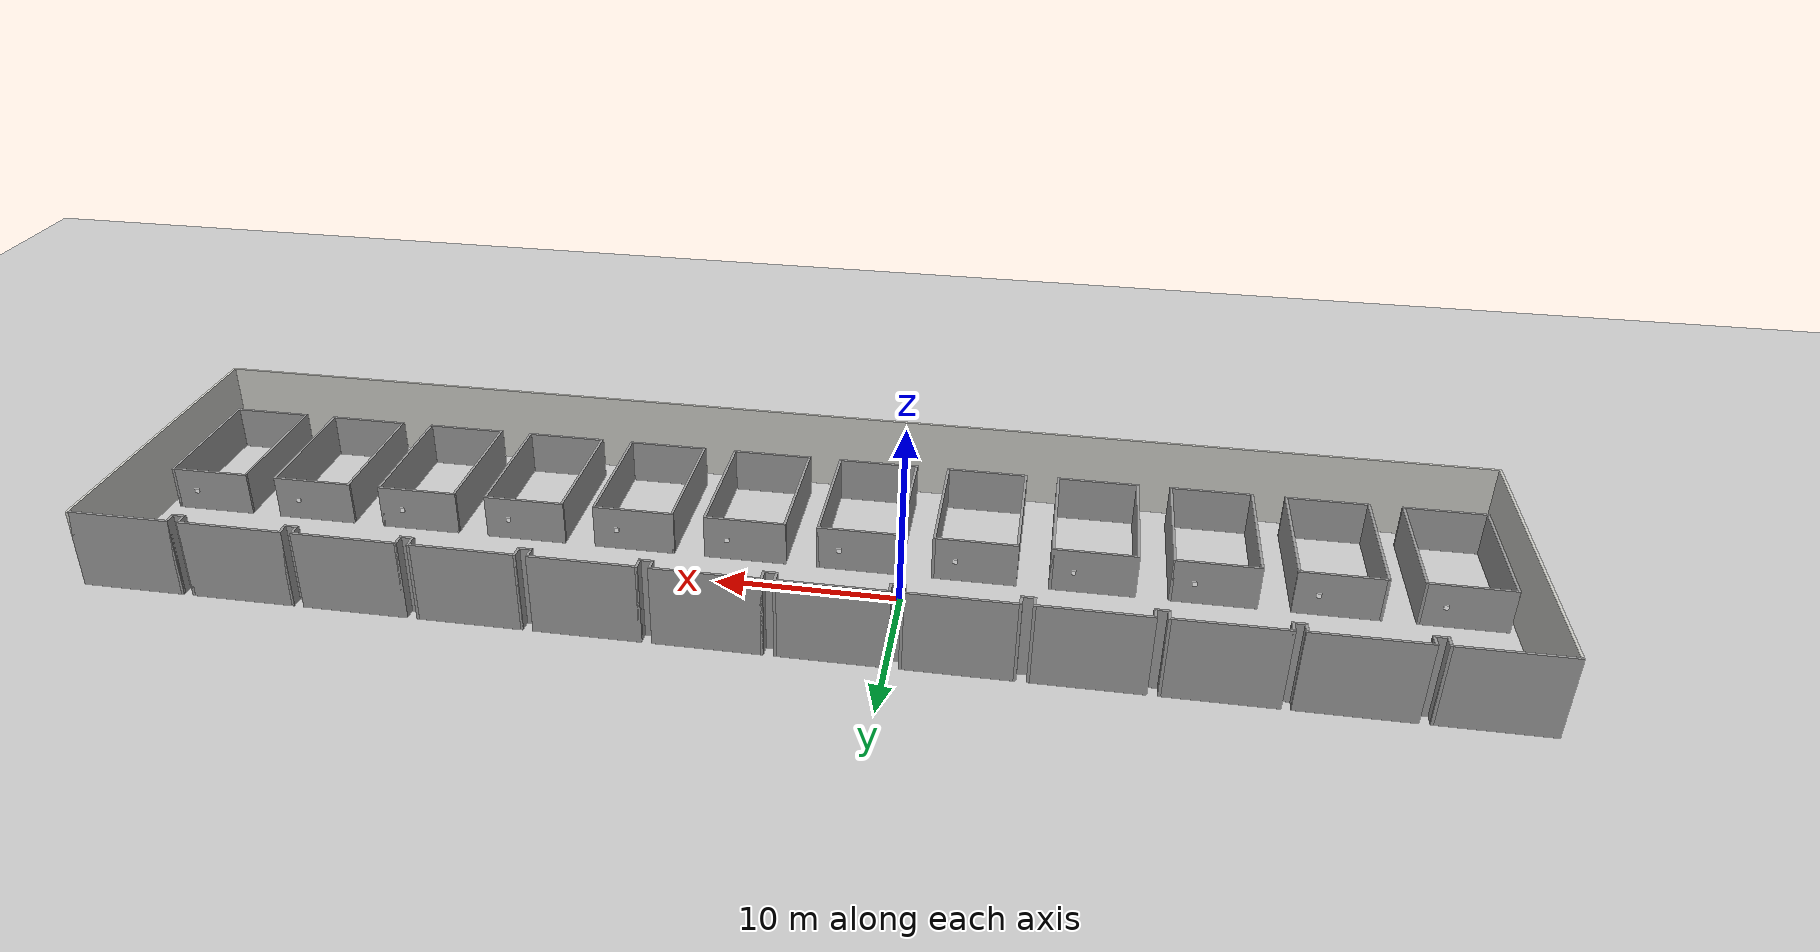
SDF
<sdf version="1.6">
 <world name="default">
  <light name="sun" type="directional">
   <pose>0 0 10 0 -0 0</pose>
   <diffuse>0.8 0.8 0.8 1</diffuse>
   <specular>0.2 0.2 0.2 1</specular>
   <attenuation>
    <range>1000</range>
    <constant>0.9</constant>
    <linear>0.01</linear>
    <quadratic>0.001</quadratic>
   </attenuation>
   <direction>-0.5 0.1 -0.9</direction>
   <spot><inner_angle>0</inner_angle><outer_angle>0</outer_angle><falloff>0</falloff></spot>
  </light>
  <model name="ground_plane">
   <static>1</static>
   <link name="link">
    <collision name="collision">
     <geometry><plane><normal>0 0 1</normal><size>100 100</size></plane></geometry>
     <surface>
      <contact><collide_bitmask>65535</collide_bitmask></contact>
      <friction><ode><mu>100</mu><mu2>50</mu2></ode></friction>
     </surface>
    </collision>
    <visual name="visual">
     <cast_shadows>0</cast_shadows>
     <geometry><plane><normal>0 0 1</normal><size>100 100</size></plane></geometry>
     <material>
      <script><uri>file://media/materials/scripts/gazebo.material</uri><name>Gazebo/Grey</name></script>
     </material>
    </visual>
   </link>
  </model>
  <gravity>0 0 -9.8</gravity>
  <magnetic_field>6e-06 2.3e-05 -4.2e-05</magnetic_field>
  <atmosphere type="adiabatic"/>
  <physics type="ode">
   <max_step_size>0.001</max_step_size>
   <real_time_factor>1</real_time_factor>
   <real_time_update_rate>1000</real_time_update_rate>
  </physics>
  <scene><ambient>0.4 0.4 0.4 1</ambient><background>0.7 0.7 0.7 1</background><shadows>1</shadows></scene>
  <spherical_coordinates>
   <surface_model>EARTH_WGS84</surface_model>
   <latitude_deg>0</latitude_deg>
   <longitude_deg>0</longitude_deg>
   <elevation>0</elevation>
   <heading_deg>0</heading_deg>
  </spherical_coordinates>
  <model name="铝厂v1">
   <pose>5.87803 -2.83421 0 0 -0 0</pose>
   <link name="Wall_10">
    <collision name="Wall_10_Collision">
     <geometry><box><size>4.6 0.15 2.5</size></box></geometry>
     <pose>0 0 1.25 0 -0 0</pose>
    </collision>
    <visual name="Wall_10_Visual">
     <pose>0 0 1.25 0 -0 0</pose>
     <geometry><box><size>4.6 0.15 2.5</size></box></geometry>
     <material>
      <script><uri>file://media/materials/scripts/gazebo.material</uri><name>Gazebo/Grey</name></script>
      <ambient>1 1 1 1</ambient>
     </material>
     <meta><layer>0</layer></meta>
    </visual>
    <pose>-9.55908 0.363094 0 0 -0 3.14159</pose>
   </link>
   <joint name="linkjoint8" type="fixed"><child>link8</child><parent>Wall_10</parent></joint>
   <link name="link8">
    <pose>-8.5 0.37 1.2 0 -0 0</pose>
    <visual name="visual8">
     <geometry><box><size>0.25 0.25 0.25</size></box></geometry>
     <material>
      <script><uri>file://media/materials/scripts/gazebo.material</uri><name>Gazebo/aruco1</name></script>
      <ambient>1 1 1 1</ambient>
     </material>
    </visual>
   </link>
   <link name="Wall_100">
    <collision name="Wall_100_Collision">
     <geometry><box><size>4.6 0.15 2.5</size></box></geometry>
     <pose>0 0 1.25 0 -0 0</pose>
    </collision>
    <visual name="Wall_100_Visual">
     <pose>0 0 1.25 0 -0 0</pose>
     <geometry><box><size>4.6 0.15 2.5</size></box></geometry>
     <material>
      <script><uri>file://media/materials/scripts/gazebo.material</uri><name>Gazebo/Grey</name></script>
      <ambient>1 1 1 1</ambient>
     </material>
     <meta><layer>0</layer></meta>
    </visual>
    <pose>21.9409 -7.48691 0 0 -0 0</pose>
   </link>
   <link name="Wall_102">
    <collision name="Wall_102_Collision">
     <geometry><box><size>8 0.15 2.5</size></box></geometry>
     <pose>0 0 1.25 0 -0 0</pose>
    </collision>
    <visual name="Wall_102_Visual">
     <pose>0 0 1.25 0 -0 0</pose>
     <geometry><box><size>8 0.15 2.5</size></box></geometry>
     <material>
      <script><uri>file://media/materials/scripts/gazebo.material</uri><name>Gazebo/Grey</name></script>
      <ambient>1 1 1 1</ambient>
     </material>
     <meta><layer>0</layer></meta>
    </visual>
    <pose>24.1659 -3.56191 0 0 -0 1.5708</pose>
   </link>
   <link name="Wall_104">
    <collision name="Wall_104_Collision">
     <geometry><box><size>8 0.15 2.5</size></box></geometry>
     <pose>0 0 1.25 0 -0 0</pose>
    </collision>
    <visual name="Wall_104_Visual">
     <pose>0 0 1.25 0 -0 0</pose>
     <geometry><box><size>8 0.15 2.5</size></box></geometry>
     <material>
      <script><uri>file://media/materials/scripts/gazebo.material</uri><name>Gazebo/Grey</name></script>
      <ambient>1 1 1 1</ambient>
     </material>
     <meta><layer>0</layer></meta>
    </visual>
    <pose>26.0159 -3.56191 0 0 -0 -1.5708</pose>
   </link>
   <link name="Wall_106">
    <collision name="Wall_106_Collision">
     <geometry><box><size>4.6 0.15 2.5</size></box></geometry>
     <pose>0 0 1.25 0 -0 0</pose>
    </collision>
    <visual name="Wall_106_Visual">
     <pose>0 0 1.25 0 -0 0</pose>
     <geometry><box><size>4.6 0.15 2.5</size></box></geometry>
     <material>
      <script><uri>file://media/materials/scripts/gazebo.material</uri><name>Gazebo/Grey</name></script>
      <ambient>1 1 1 1</ambient>
     </material>
     <meta><layer>0</layer></meta>
    </visual>
    <pose>28.2409 -7.48691 0 0 -0 0</pose>
   </link>
   <link name="Wall_109">
    <collision name="Wall_109_Collision">
     <geometry><box><size>8 0.15 2.5</size></box></geometry>
     <pose>0 0 1.25 0 -0 0</pose>
    </collision>
    <visual name="Wall_109_Visual">
     <pose>0 0 1.25 0 -0 0</pose>
     <geometry><box><size>8 0.15 2.5</size></box></geometry>
     <material>
      <script><uri>file://media/materials/scripts/gazebo.material</uri><name>Gazebo/Grey</name></script>
      <ambient>1 1 1 1</ambient>
     </material>
     <meta><layer>0</layer></meta>
    </visual>
    <pose>30.4659 -3.56191 0 0 -0 1.5708</pose>
   </link>
   <link name="Wall_112">
    <collision name="Wall_112_Collision">
     <geometry><box><size>8 0.15 2.5</size></box></geometry>
     <pose>0 0 1.25 0 -0 0</pose>
    </collision>
    <visual name="Wall_112_Visual">
     <pose>0 0 1.25 0 -0 0</pose>
     <geometry><box><size>8 0.15 2.5</size></box></geometry>
     <material>
      <script><uri>file://media/materials/scripts/gazebo.material</uri><name>Gazebo/Grey</name></script>
      <ambient>1 1 1 1</ambient>
     </material>
     <meta><layer>0</layer></meta>
    </visual>
    <pose>32.3159 -3.56191 0 0 -0 -1.5708</pose>
   </link>
   <link name="Wall_113">
    <collision name="Wall_113_Collision">
     <geometry><box><size>4.6 0.15 2.5</size></box></geometry>
     <pose>0 0 1.25 0 -0 0</pose>
    </collision>
    <visual name="Wall_113_Visual">
     <pose>0 0 1.25 0 -0 0</pose>
     <geometry><box><size>4.6 0.15 2.5</size></box></geometry>
     <material>
      <script><uri>file://media/materials/scripts/gazebo.material</uri><name>Gazebo/Grey</name></script>
      <ambient>1 1 1 1</ambient>
     </material>
     <meta><layer>0</layer></meta>
    </visual>
    <pose>34.5409 -7.48691 0 0 -0 0</pose>
   </link>
   <link name="Wall_115">
    <collision name="Wall_115_Collision">
     <geometry><box><size>8 0.15 2.5</size></box></geometry>
     <pose>0 0 1.25 0 -0 0</pose>
    </collision>
    <visual name="Wall_115_Visual">
     <pose>0 0 1.25 0 -0 0</pose>
     <geometry><box><size>8 0.15 2.5</size></box></geometry>
     <material>
      <script><uri>file://media/materials/scripts/gazebo.material</uri><name>Gazebo/Grey</name></script>
      <ambient>1 1 1 1</ambient>
     </material>
     <meta><layer>0</layer></meta>
    </visual>
    <pose>36.7659 -3.56191 0 0 -0 1.5708</pose>
   </link>
   <link name="Wall_117">
    <collision name="Wall_117_Collision">
     <geometry><box><size>4.6 0.15 2.5</size></box></geometry>
     <pose>0 0 1.25 0 -0 0</pose>
    </collision>
    <visual name="Wall_117_Visual">
     <pose>0 0 1.25 0 -0 0</pose>
     <geometry><box><size>4.6 0.15 2.5</size></box></geometry>
     <material>
      <script><uri>file://media/materials/scripts/gazebo.material</uri><name>Gazebo/Grey</name></script>
      <ambient>1 1 1 1</ambient>
     </material>
     <meta><layer>0</layer></meta>
    </visual>
    <pose>34.5409 0.363094 0 0 -0 3.14159</pose>
   </link>
   <joint name="linkjoint1" type="fixed"><child>link1</child><parent>Wall_117</parent></joint>
   <link name="link1">
    <pose>35.5 0.37 1.2 0 -0 0</pose>
    <visual name="visual1">
     <geometry><box><size>0.25 0.25 0.25</size></box></geometry>
     <material>
      <script><uri>file://media/materials/scripts/gazebo.material</uri><name>Gazebo/aruco1</name></script>
      <ambient>1 1 1 1</ambient>
     </material>
    </visual>
   </link>
   <link name="Wall_119">
    <collision name="Wall_119_Collision">
     <geometry><box><size>4.6 0.15 2.5</size></box></geometry>
     <pose>0 0 1.25 0 -0 0</pose>
    </collision>
    <visual name="Wall_119_Visual">
     <pose>0 0 1.25 0 -0 0</pose>
     <geometry><box><size>4.6 0.15 2.5</size></box></geometry>
     <material>
      <script><uri>file://media/materials/scripts/gazebo.material</uri><name>Gazebo/Grey</name></script>
      <ambient>1 1 1 1</ambient>
     </material>
     <meta><layer>0</layer></meta>
    </visual>
    <pose>28.2409 0.363094 0 0 -0 0</pose>
   </link>
   <joint name="linkjoint2" type="fixed"><child>link2</child><parent>Wall_119</parent></joint>
   <link name="link2">
    <pose>29.2 0.37 1.2 0 -0 0</pose>
    <visual name="visual2">
     <geometry><box><size>0.25 0.25 0.25</size></box></geometry>
     <material>
      <script><uri>file://media/materials/scripts/gazebo.material</uri><name>Gazebo/aruco1</name></script>
      <ambient>1 1 1 1</ambient>
     </material>
    </visual>
   </link>
   <link name="Wall_121">
    <collision name="Wall_121_Collision">
     <geometry><box><size>4.6 0.15 2.5</size></box></geometry>
     <pose>0 0 1.25 0 -0 0</pose>
    </collision>
    <visual name="Wall_121_Visual">
     <pose>0 0 1.25 0 -0 0</pose>
     <geometry><box><size>4.6 0.15 2.5</size></box></geometry>
     <material>
      <script><uri>file://media/materials/scripts/gazebo.material</uri><name>Gazebo/Grey</name></script>
      <ambient>1 1 1 1</ambient>
     </material>
     <meta><layer>0</layer></meta>
    </visual>
    <pose>21.9409 0.363094 0 0 -0 0</pose>
   </link>
   <joint name="linkjoint3" type="fixed"><child>link3</child><parent>Wall_121</parent></joint>
   <link name="link3">
    <pose>22.9 0.37 1.2 0 -0 0</pose>
    <visual name="visual3">
     <geometry><box><size>0.25 0.25 0.25</size></box></geometry>
     <material>
      <script><uri>file://media/materials/scripts/gazebo.material</uri><name>Gazebo/aruco1</name></script>
      <ambient>1 1 1 1</ambient>
     </material>
    </visual>
   </link>
   <link name="Wall_123">
    <collision name="Wall_123_Collision">
     <geometry><box><size>4.6 0.15 2.5</size></box></geometry>
     <pose>0 0 1.25 0 -0 0</pose>
    </collision>
    <visual name="Wall_123_Visual">
     <pose>0 0 1.25 0 -0 0</pose>
     <geometry><box><size>4.6 0.15 2.5</size></box></geometry>
     <material>
      <script><uri>file://media/materials/scripts/gazebo.material</uri><name>Gazebo/Grey</name></script>
      <ambient>1 1 1 1</ambient>
     </material>
     <meta><layer>0</layer></meta>
    </visual>
    <pose>15.6409 0.363094 0 0 -0 0</pose>
   </link>
   <joint name="linkjoint4" type="fixed"><child>link4</child><parent>Wall_123</parent></joint>
   <link name="link4">
    <pose>16.6 0.37 1.2 0 -0 0</pose>
    <visual name="visual4">
     <geometry><box><size>0.25 0.25 0.25</size></box></geometry>
     <material>
      <script><uri>file://media/materials/scripts/gazebo.material</uri><name>Gazebo/aruco1</name></script>
      <ambient>1 1 1 1</ambient>
     </material>
    </visual>
   </link>
   <link name="Wall_125">
    <collision name="Wall_125_Collision">
     <geometry><box><size>4.6 0.15 2.5</size></box></geometry>
     <pose>0 0 1.25 0 -0 0</pose>
    </collision>
    <visual name="Wall_125_Visual">
     <pose>0 0 1.25 0 -0 0</pose>
     <geometry><box><size>4.6 0.15 2.5</size></box></geometry>
     <material>
      <script><uri>file://media/materials/scripts/gazebo.material</uri><name>Gazebo/Grey</name></script>
      <ambient>1 1 1 1</ambient>
     </material>
     <meta><layer>0</layer></meta>
    </visual>
    <pose>9.34092 0.363094 0 0 -0 0</pose>
   </link>
   <joint name="linkjoint5" type="fixed"><child>link5</child><parent>Wall_125</parent></joint>
   <link name="link5">
    <pose>10.3 0.37 1.2 0 -0 0</pose>
    <visual name="visual5">
     <geometry><box><size>0.25 0.25 0.25</size></box></geometry>
     <material>
      <script><uri>file://media/materials/scripts/gazebo.material</uri><name>Gazebo/aruco1</name></script>
      <ambient>1 1 1 1</ambient>
     </material>
    </visual>
   </link>
   <link name="Wall_127">
    <collision name="Wall_127_Collision">
     <geometry><box><size>4.6 0.15 2.5</size></box></geometry>
     <pose>0 0 1.25 0 -0 0</pose>
    </collision>
    <visual name="Wall_127_Visual">
     <pose>0 0 1.25 0 -0 0</pose>
     <geometry><box><size>4.6 0.15 2.5</size></box></geometry>
     <material>
      <script><uri>file://media/materials/scripts/gazebo.material</uri><name>Gazebo/Grey</name></script>
      <ambient>1 1 1 1</ambient>
     </material>
     <meta><layer>0</layer></meta>
    </visual>
    <pose>3.04092 0.363094 0 0 -0 0</pose>
   </link>
   <joint name="linkjoint6" type="fixed"><child>link6</child><parent>Wall_127</parent></joint>
   <link name="link6">
    <pose>4.04 0.37 1.2 0 -0 0</pose>
    <visual name="visual6">
     <geometry><box><size>0.25 0.25 0.25</size></box></geometry>
     <material>
      <script><uri>file://media/materials/scripts/gazebo.material</uri><name>Gazebo/aruco1</name></script>
      <ambient>1 1 1 1</ambient>
     </material>
    </visual>
   </link>
   <link name="Wall_13">
    <collision name="Wall_13_Collision">
     <geometry><box><size>8 0.15 2.5</size></box></geometry>
     <pose>0 0 1.25 0 -0 0</pose>
    </collision>
    <visual name="Wall_13_Visual">
     <pose>0 0 1.25 0 -0 0</pose>
     <geometry><box><size>8 0.15 2.5</size></box></geometry>
     <material>
      <script><uri>file://media/materials/scripts/gazebo.material</uri><name>Gazebo/Grey</name></script>
      <ambient>1 1 1 1</ambient>
     </material>
     <meta><layer>0</layer></meta>
    </visual>
    <pose>-11.7841 -3.56191 0 0 -0 -1.5708</pose>
   </link>
   <link name="Wall_17">
    <collision name="Wall_17_Collision">
     <geometry><box><size>8 0.15 2.5</size></box></geometry>
     <pose>0 0 1.25 0 -0 0</pose>
    </collision>
    <visual name="Wall_17_Visual">
     <pose>0 0 1.25 0 -0 0</pose>
     <geometry><box><size>8 0.15 2.5</size></box></geometry>
     <material>
      <script><uri>file://media/materials/scripts/gazebo.material</uri><name>Gazebo/Grey</name></script>
      <ambient>1 1 1 1</ambient>
     </material>
     <meta><layer>0</layer></meta>
    </visual>
    <pose>-13.6341 -3.56191 0 0 -0 -1.5708</pose>
   </link>
   <link name="Wall_19">
    <collision name="Wall_19_Collision">
     <geometry><box><size>4.6 0.15 2.5</size></box></geometry>
     <pose>0 0 1.25 0 -0 0</pose>
    </collision>
    <visual name="Wall_19_Visual">
     <pose>0 0 1.25 0 -0 0</pose>
     <geometry><box><size>4.6 0.15 2.5</size></box></geometry>
     <material>
      <script><uri>file://media/materials/scripts/gazebo.material</uri><name>Gazebo/Grey</name></script>
      <ambient>1 1 1 1</ambient>
     </material>
     <meta><layer>0</layer></meta>
    </visual>
    <pose>-15.8591 0.363094 0 0 -0 3.14159</pose>
   </link>
   <joint name="linkjoint9" type="fixed"><child>link9</child><parent>Wall_19</parent></joint>
   <link name="link9">
    <pose>-14.8 0.37 1.2 0 -0 0</pose>
    <visual name="visual9">
     <geometry><box><size>0.25 0.25 0.25</size></box></geometry>
     <material>
      <script><uri>file://media/materials/scripts/gazebo.material</uri><name>Gazebo/aruco1</name></script>
      <ambient>1 1 1 1</ambient>
     </material>
    </visual>
   </link>
   <link name="Wall_21">
    <collision name="Wall_21_Collision">
     <geometry><box><size>8 0.15 2.5</size></box></geometry>
     <pose>0 0 1.25 0 -0 0</pose>
    </collision>
    <visual name="Wall_21_Visual">
     <pose>0 0 1.25 0 -0 0</pose>
     <geometry><box><size>8 0.15 2.5</size></box></geometry>
     <material>
      <script><uri>file://media/materials/scripts/gazebo.material</uri><name>Gazebo/Grey</name></script>
      <ambient>1 1 1 1</ambient>
     </material>
     <meta><layer>0</layer></meta>
    </visual>
    <pose>-18.0841 -3.56191 0 0 -0 -1.5708</pose>
   </link>
   <link name="Wall_211">
    <collision name="Wall_211_Collision">
     <geometry><box><size>2.5 0.15 1</size></box></geometry>
     <pose>0 0 0.5 0 -0 0</pose>
    </collision>
    <visual name="Wall_211_Visual">
     <pose>0 0 0.5 0 -0 0</pose>
     <geometry><box><size>2.5 0.15 1</size></box></geometry>
     <material>
      <script><uri>file://media/materials/scripts/gazebo.material</uri><name>Gazebo/CeilingTiled</name></script>
      <ambient>1 1 1 1</ambient>
     </material>
     <meta><layer>0</layer></meta>
    </visual>
    <pose>-8.488 5.46188 0 0 -0 0</pose>
   </link>
   <link name="Wall_213">
    <collision name="Wall_213_Collision">
     <geometry><box><size>2 0.15 1</size></box></geometry>
     <pose>0 0 0.5 0 -0 0</pose>
    </collision>
    <visual name="Wall_213_Visual">
     <pose>0 0 0.5 0 -0 0</pose>
     <geometry><box><size>2 0.15 1</size></box></geometry>
     <material>
      <script><uri>file://media/materials/scripts/gazebo.material</uri><name>Gazebo/CeilingTiled</name></script>
      <ambient>1 1 1 1</ambient>
     </material>
     <meta><layer>0</layer></meta>
    </visual>
    <pose>-7.313 6.38688 0 0 -0 1.5708</pose>
   </link>
   <link name="Wall_214">
    <collision name="Wall_214_Collision">
     <geometry><box><size>5 0.15 1</size></box></geometry>
     <pose>0 0 0.5 0 -0 0</pose>
    </collision>
    <visual name="Wall_214_Visual">
     <pose>0 0 0.5 0 -0 0</pose>
     <geometry><box><size>5 0.15 1</size></box></geometry>
     <material>
      <script><uri>file://media/materials/scripts/gazebo.material</uri><name>Gazebo/CeilingTiled</name></script>
      <ambient>1 1 1 1</ambient>
     </material>
     <meta><layer>0</layer></meta>
    </visual>
    <pose>-9.738 7.31188 0 0 -0 3.14159</pose>
   </link>
   <link name="Wall_215">
    <collision name="Wall_215_Collision">
     <geometry><box><size>2 0.15 1</size></box></geometry>
     <pose>0 0 0.5 0 -0 0</pose>
    </collision>
    <visual name="Wall_215_Visual">
     <pose>0 0 0.5 0 -0 0</pose>
     <geometry><box><size>2 0.15 1</size></box></geometry>
     <material>
      <script><uri>file://media/materials/scripts/gazebo.material</uri><name>Gazebo/CeilingTiled</name></script>
      <ambient>1 1 1 1</ambient>
     </material>
     <meta><layer>0</layer></meta>
    </visual>
    <pose>-12.163 6.38688 0 0 -0 -1.5708</pose>
   </link>
   <link name="Wall_216">
    <collision name="Wall_216_Collision">
     <geometry><box><size>2.65 0.15 1</size></box></geometry>
     <pose>0 0 0.5 0 -0 0</pose>
    </collision>
    <visual name="Wall_216_Visual">
     <pose>0 0 0.5 0 -0 0</pose>
     <geometry><box><size>2.65 0.15 1</size></box></geometry>
     <material>
      <script><uri>file://media/materials/scripts/gazebo.material</uri><name>Gazebo/CeilingTiled</name></script>
      <ambient>1 1 1 1</ambient>
     </material>
     <meta><layer>0</layer></meta>
    </visual>
    <pose>-10.913 5.46188 0 0 -0 0</pose>
   </link>
   <link name="Wall_220">
    <collision name="Wall_220_Collision">
     <geometry><box><size>1 0.15 1</size></box></geometry>
     <pose>0 0 0.5 0 -0 0</pose>
    </collision>
    <visual name="Wall_220_Visual">
     <pose>0 0 0.5 0 -0 0</pose>
     <geometry><box><size>1 0.15 1</size></box></geometry>
     <material>
      <script><uri>file://media/materials/scripts/gazebo.material</uri><name>Gazebo/CeilingTiled</name></script>
      <ambient>1 1 1 1</ambient>
     </material>
     <meta><layer>0</layer></meta>
    </visual>
    <pose>6.934 6.05488 0 0 -0 -1.5708</pose>
   </link>
   <link name="Wall_221">
    <collision name="Wall_221_Collision">
     <geometry><box><size>5 0.15 1</size></box></geometry>
     <pose>0 0 0.5 0 -0 0</pose>
    </collision>
    <visual name="Wall_221_Visual">
     <pose>0 0 0.5 0 -0 0</pose>
     <geometry><box><size>5 0.15 1</size></box></geometry>
     <material>
      <script><uri>file://media/materials/scripts/gazebo.material</uri><name>Gazebo/CeilingTiled</name></script>
      <ambient>1 1 1 1</ambient>
     </material>
     <meta><layer>0</layer></meta>
    </visual>
    <pose>9.359 5.62988 0 0 -0 0</pose>
   </link>
   <link name="Wall_222">
    <collision name="Wall_222_Collision">
     <geometry><box><size>2 0.15 1</size></box></geometry>
     <pose>0 0 0.5 0 -0 0</pose>
    </collision>
    <visual name="Wall_222_Visual">
     <pose>0 0 0.5 0 -0 0</pose>
     <geometry><box><size>2 0.15 1</size></box></geometry>
     <material>
      <script><uri>file://media/materials/scripts/gazebo.material</uri><name>Gazebo/CeilingTiled</name></script>
      <ambient>1 1 1 1</ambient>
     </material>
     <meta><layer>0</layer></meta>
    </visual>
    <pose>11.784 6.55488 0 0 -0 1.5708</pose>
   </link>
   <link name="Wall_223">
    <collision name="Wall_223_Collision">
     <geometry><box><size>5 0.15 1</size></box></geometry>
     <pose>0 0 0.5 0 -0 0</pose>
    </collision>
    <visual name="Wall_223_Visual">
     <pose>0 0 0.5 0 -0 0</pose>
     <geometry><box><size>5 0.15 1</size></box></geometry>
     <material>
      <script><uri>file://media/materials/scripts/gazebo.material</uri><name>Gazebo/CeilingTiled</name></script>
      <ambient>1 1 1 1</ambient>
     </material>
     <meta><layer>0</layer></meta>
    </visual>
    <pose>9.359 7.47988 0 0 -0 3.14159</pose>
   </link>
   <link name="Wall_224">
    <collision name="Wall_224_Collision">
     <geometry><box><size>1.15 0.15 1</size></box></geometry>
     <pose>0 0 0.5 0 -0 0</pose>
    </collision>
    <visual name="Wall_224_Visual">
     <pose>0 0 0.5 0 -0 0</pose>
     <geometry><box><size>1.15 0.15 1</size></box></geometry>
     <material>
      <script><uri>file://media/materials/scripts/gazebo.material</uri><name>Gazebo/CeilingTiled</name></script>
      <ambient>1 1 1 1</ambient>
     </material>
     <meta><layer>0</layer></meta>
    </visual>
    <pose>6.934 6.97988 0 0 -0 -1.5708</pose>
   </link>
   <link name="Wall_228">
    <collision name="Wall_228_Collision">
     <geometry><box><size>1 0.15 1</size></box></geometry>
     <pose>0 0 0.5 0 -0 0</pose>
    </collision>
    <visual name="Wall_228_Visual">
     <pose>0 0 0.5 0 -0 0</pose>
     <geometry><box><size>1 0.15 1</size></box></geometry>
     <material>
      <script><uri>file://media/materials/scripts/gazebo.material</uri><name>Gazebo/CeilingTiled</name></script>
      <ambient>1 1 1 1</ambient>
     </material>
     <meta><layer>0</layer></meta>
    </visual>
    <pose>26.022 6.16788 0 0 -0 -1.5708</pose>
   </link>
   <link name="Wall_229">
    <collision name="Wall_229_Collision">
     <geometry><box><size>5 0.15 1</size></box></geometry>
     <pose>0 0 0.5 0 -0 0</pose>
    </collision>
    <visual name="Wall_229_Visual">
     <pose>0 0 0.5 0 -0 0</pose>
     <geometry><box><size>5 0.15 1</size></box></geometry>
     <material>
      <script><uri>file://media/materials/scripts/gazebo.material</uri><name>Gazebo/CeilingTiled</name></script>
      <ambient>1 1 1 1</ambient>
     </material>
     <meta><layer>0</layer></meta>
    </visual>
    <pose>28.447 5.74288 0 0 -0 0</pose>
   </link>
   <link name="Wall_231">
    <collision name="Wall_231_Collision">
     <geometry><box><size>2 0.15 1</size></box></geometry>
     <pose>0 0 0.5 0 -0 0</pose>
    </collision>
    <visual name="Wall_231_Visual">
     <pose>0 0 0.5 0 -0 0</pose>
     <geometry><box><size>2 0.15 1</size></box></geometry>
     <material>
      <script><uri>file://media/materials/scripts/gazebo.material</uri><name>Gazebo/CeilingTiled</name></script>
      <ambient>1 1 1 1</ambient>
     </material>
     <meta><layer>0</layer></meta>
    </visual>
    <pose>30.872 6.66788 0 0 -0 1.5708</pose>
   </link>
   <link name="Wall_233">
    <collision name="Wall_233_Collision">
     <geometry><box><size>5 0.15 1</size></box></geometry>
     <pose>0 0 0.5 0 -0 0</pose>
    </collision>
    <visual name="Wall_233_Visual">
     <pose>0 0 0.5 0 -0 0</pose>
     <geometry><box><size>5 0.15 1</size></box></geometry>
     <material>
      <script><uri>file://media/materials/scripts/gazebo.material</uri><name>Gazebo/CeilingTiled</name></script>
      <ambient>1 1 1 1</ambient>
     </material>
     <meta><layer>0</layer></meta>
    </visual>
    <pose>28.447 7.59288 0 0 -0 3.14159</pose>
   </link>
   <link name="Wall_235">
    <collision name="Wall_235_Collision">
     <geometry><box><size>1.15 0.15 1</size></box></geometry>
     <pose>0 0 0.5 0 -0 0</pose>
    </collision>
    <visual name="Wall_235_Visual">
     <pose>0 0 0.5 0 -0 0</pose>
     <geometry><box><size>1.15 0.15 1</size></box></geometry>
     <material>
      <script><uri>file://media/materials/scripts/gazebo.material</uri><name>Gazebo/CeilingTiled</name></script>
      <ambient>1 1 1 1</ambient>
     </material>
     <meta><layer>0</layer></meta>
    </visual>
    <pose>26.022 7.09288 0 0 -0 -1.5708</pose>
   </link>
   <link name="Wall_239">
    <collision name="Wall_239_Collision">
     <geometry><box><size>1 0.15 1</size></box></geometry>
     <pose>0 0 0.5 0 -0 0</pose>
    </collision>
    <visual name="Wall_239_Visual">
     <pose>0 0 0.5 0 -0 0</pose>
     <geometry><box><size>1 0.15 1</size></box></geometry>
     <material>
      <script><uri>file://media/materials/scripts/gazebo.material</uri><name>Gazebo/CeilingTiled</name></script>
      <ambient>1 1 1 1</ambient>
     </material>
     <meta><layer>0</layer></meta>
    </visual>
    <pose>-26.346 5.99087 0 0 -0 -1.57089</pose>
   </link>
   <link name="Wall_24">
    <collision name="Wall_24_Collision">
     <geometry><box><size>8 0.15 2.5</size></box></geometry>
     <pose>0 0 1.25 0 -0 0</pose>
    </collision>
    <visual name="Wall_24_Visual">
     <pose>0 0 1.25 0 -0 0</pose>
     <geometry><box><size>8 0.15 2.5</size></box></geometry>
     <material>
      <script><uri>file://media/materials/scripts/gazebo.material</uri><name>Gazebo/Grey</name></script>
      <ambient>1 1 1 1</ambient>
     </material>
     <meta><layer>0</layer></meta>
    </visual>
    <pose>-19.9341 -3.56191 0 0 -0 -1.5708</pose>
   </link>
   <link name="Wall_241">
    <collision name="Wall_241_Collision">
     <geometry><box><size>5 0.15 1</size></box></geometry>
     <pose>0 0 0.5 0 -0 0</pose>
    </collision>
    <visual name="Wall_241_Visual">
     <pose>0 0 0.5 0 -0 0</pose>
     <geometry><box><size>5 0.15 1</size></box></geometry>
     <material>
      <script><uri>file://media/materials/scripts/gazebo.material</uri><name>Gazebo/CeilingTiled</name></script>
      <ambient>1 1 1 1</ambient>
     </material>
     <meta><layer>0</layer></meta>
    </visual>
    <pose>-28.7711 5.56586 0 0 -0 3.14159</pose>
   </link>
   <link name="Wall_243">
    <collision name="Wall_243_Collision">
     <geometry><box><size>2 0.15 1</size></box></geometry>
     <pose>0 0 0.5 0 -0 0</pose>
    </collision>
    <visual name="Wall_243_Visual">
     <pose>0 0 0.5 0 -0 0</pose>
     <geometry><box><size>2 0.15 1</size></box></geometry>
     <material>
      <script><uri>file://media/materials/scripts/gazebo.material</uri><name>Gazebo/CeilingTiled</name></script>
      <ambient>1 1 1 1</ambient>
     </material>
     <meta><layer>0</layer></meta>
    </visual>
    <pose>-31.196 6.49087 0 0 -0 1.57075</pose>
   </link>
   <link name="Wall_245">
    <collision name="Wall_245_Collision">
     <geometry><box><size>5 0.15 1</size></box></geometry>
     <pose>0 0 0.5 0 -0 0</pose>
    </collision>
    <visual name="Wall_245_Visual">
     <pose>0 0 0.5 0 -0 0</pose>
     <geometry><box><size>5 0.15 1</size></box></geometry>
     <material>
      <script><uri>file://media/materials/scripts/gazebo.material</uri><name>Gazebo/CeilingTiled</name></script>
      <ambient>1 1 1 1</ambient>
     </material>
     <meta><layer>0</layer></meta>
    </visual>
    <pose>-28.771 7.41588 0 0 -0 0</pose>
   </link>
   <link name="Wall_247">
    <collision name="Wall_247_Collision">
     <geometry><box><size>1.15002 0.15 1</size></box></geometry>
     <pose>0 0 0.5 0 -0 0</pose>
    </collision>
    <visual name="Wall_247_Visual">
     <pose>0 0 0.5 0 -0 0</pose>
     <geometry><box><size>1.15002 0.15 1</size></box></geometry>
     <material>
      <script><uri>file://media/materials/scripts/gazebo.material</uri><name>Gazebo/CeilingTiled</name></script>
      <ambient>1 1 1 1</ambient>
     </material>
     <meta><layer>0</layer></meta>
    </visual>
    <pose>-26.346 6.91588 0 0 -0 -1.5708</pose>
   </link>
   <link name="Wall_253">
    <collision name="Wall_253_Collision">
     <geometry><box><size>0.8 0.15 4.5</size></box></geometry>
     <pose>0 0 2.25 0 -0 0</pose>
    </collision>
    <visual name="Wall_253_Visual">
     <pose>0 0 2.25 0 -0 0</pose>
     <geometry><box><size>0.8 0.15 4.5</size></box></geometry>
     <material>
      <script><uri>file://media/materials/scripts/gazebo.material</uri><name>Gazebo/Grey</name></script>
      <ambient>1 1 1 1</ambient>
     </material>
     <meta><layer>0</layer></meta>
    </visual>
    <pose>-0.324999 8.72488 0 0 -0 1.5708</pose>
   </link>
   <link name="Wall_257">
    <collision name="Wall_257_Collision">
     <geometry><box><size>0.8 0.15 4.5</size></box></geometry>
     <pose>0 0 2.25 0 -0 0</pose>
    </collision>
    <visual name="Wall_257_Visual">
     <pose>0 0 2.25 0 -0 0</pose>
     <geometry><box><size>0.8 0.15 4.5</size></box></geometry>
     <material>
      <script><uri>file://media/materials/scripts/gazebo.material</uri><name>Gazebo/Grey</name></script>
      <ambient>1 1 1 1</ambient>
     </material>
     <meta><layer>0</layer></meta>
    </visual>
    <pose>1e-06 8.39988 0 0 -0 0</pose>
   </link>
   <link name="Wall_259">
    <collision name="Wall_259_Collision">
     <geometry><box><size>5.8 0.15 4.5</size></box></geometry>
     <pose>0 0 2.25 0 -0 0</pose>
    </collision>
    <visual name="Wall_259_Visual">
     <pose>0 0 2.25 0 -0 0</pose>
     <geometry><box><size>5.8 0.15 4.5</size></box></geometry>
     <material>
      <script><uri>file://media/materials/scripts/gazebo.material</uri><name>Gazebo/Grey</name></script>
      <ambient>1 1 1 1</ambient>
     </material>
     <meta><layer>0</layer></meta>
    </visual>
    <pose>-3.15 9.04988 0 0 -0 3.14159</pose>
   </link>
   <link name="Wall_26">
    <collision name="Wall_26_Collision">
     <geometry><box><size>4.6 0.15 2.5</size></box></geometry>
     <pose>0 0 1.25 0 -0 0</pose>
    </collision>
    <visual name="Wall_26_Visual">
     <pose>0 0 1.25 0 -0 0</pose>
     <geometry><box><size>4.6 0.15 2.5</size></box></geometry>
     <material>
      <script><uri>file://media/materials/scripts/gazebo.material</uri><name>Gazebo/Grey</name></script>
      <ambient>1 1 1 1</ambient>
     </material>
     <meta><layer>0</layer></meta>
    </visual>
    <pose>-22.1591 0.363094 0 0 -0 3.14159</pose>
   </link>
   <joint name="linkjoint10" type="fixed"><child>link10</child><parent>Wall_26</parent></joint>
   <link name="link10">
    <pose>-21.1 0.37 1.2 0 -0 0</pose>
    <visual name="visual10">
     <geometry><box><size>0.25 0.25 0.25</size></box></geometry>
     <material>
      <script><uri>file://media/materials/scripts/gazebo.material</uri><name>Gazebo/aruco1</name></script>
      <ambient>1 1 1 1</ambient>
     </material>
    </visual>
   </link>
   <link name="Wall_261">
    <collision name="Wall_261_Collision">
     <geometry><box><size>0.8 0.15 4.5</size></box></geometry>
     <pose>0 0 2.25 0 -0 0</pose>
    </collision>
    <visual name="Wall_261_Visual">
     <pose>0 0 2.25 0 -0 0</pose>
     <geometry><box><size>0.8 0.15 4.5</size></box></geometry>
     <material>
      <script><uri>file://media/materials/scripts/gazebo.material</uri><name>Gazebo/Grey</name></script>
      <ambient>1 1 1 1</ambient>
     </material>
     <meta><layer>0</layer></meta>
    </visual>
    <pose>-5.975 8.72488 0 0 -0 -1.5708</pose>
   </link>
   <link name="Wall_263">
    <collision name="Wall_263_Collision">
     <geometry><box><size>0.8 0.15 4.5</size></box></geometry>
     <pose>0 0 2.25 0 -0 0</pose>
    </collision>
    <visual name="Wall_263_Visual">
     <pose>0 0 2.25 0 -0 0</pose>
     <geometry><box><size>0.8 0.15 4.5</size></box></geometry>
     <material>
      <script><uri>file://media/materials/scripts/gazebo.material</uri><name>Gazebo/Grey</name></script>
      <ambient>1 1 1 1</ambient>
     </material>
     <meta><layer>0</layer></meta>
    </visual>
    <pose>-6.3 8.39988 0 0 -0 3.14159</pose>
   </link>
   <link name="Wall_265">
    <collision name="Wall_265_Collision">
     <geometry><box><size>0.8 0.15 4.5</size></box></geometry>
     <pose>0 0 2.25 0 -0 0</pose>
    </collision>
    <visual name="Wall_265_Visual">
     <pose>0 0 2.25 0 -0 0</pose>
     <geometry><box><size>0.8 0.15 4.5</size></box></geometry>
     <material>
      <script><uri>file://media/materials/scripts/gazebo.material</uri><name>Gazebo/Grey</name></script>
      <ambient>1 1 1 1</ambient>
     </material>
     <meta><layer>0</layer></meta>
    </visual>
    <pose>-6.625 8.72488 0 0 -0 1.5708</pose>
   </link>
   <link name="Wall_267">
    <collision name="Wall_267_Collision">
     <geometry><box><size>5.8 0.15 4.5</size></box></geometry>
     <pose>0 0 2.25 0 -0 0</pose>
    </collision>
    <visual name="Wall_267_Visual">
     <pose>0 0 2.25 0 -0 0</pose>
     <geometry><box><size>5.8 0.15 4.5</size></box></geometry>
     <material>
      <script><uri>file://media/materials/scripts/gazebo.material</uri><name>Gazebo/Grey</name></script>
      <ambient>1 1 1 1</ambient>
     </material>
     <meta><layer>0</layer></meta>
    </visual>
    <pose>-9.45 9.04988 0 0 -0 3.14159</pose>
   </link>
   <link name="Wall_275">
    <collision name="Wall_275_Collision">
     <geometry><box><size>5.8 0.15 4.5</size></box></geometry>
     <pose>0 0 2.25 0 -0 0</pose>
    </collision>
    <visual name="Wall_275_Visual">
     <pose>0 0 2.25 0 -0 0</pose>
     <geometry><box><size>5.8 0.15 4.5</size></box></geometry>
     <material>
      <script><uri>file://media/materials/scripts/gazebo.material</uri><name>Gazebo/Grey</name></script>
      <ambient>1 1 1 1</ambient>
     </material>
     <meta><layer>0</layer></meta>
    </visual>
    <pose>-15.75 9.04988 0 0 -0 3.14159</pose>
   </link>
   <link name="Wall_277">
    <collision name="Wall_277_Collision">
     <geometry><box><size>0.8 0.15 4.5</size></box></geometry>
     <pose>0 0 2.25 0 -0 0</pose>
    </collision>
    <visual name="Wall_277_Visual">
     <pose>0 0 2.25 0 -0 0</pose>
     <geometry><box><size>0.8 0.15 4.5</size></box></geometry>
     <material>
      <script><uri>file://media/materials/scripts/gazebo.material</uri><name>Gazebo/Grey</name></script>
      <ambient>1 1 1 1</ambient>
     </material>
     <meta><layer>0</layer></meta>
    </visual>
    <pose>-18.575 8.72488 0 0 -0 -1.5708</pose>
   </link>
   <link name="Wall_279">
    <collision name="Wall_279_Collision">
     <geometry><box><size>0.8 0.15 4.5</size></box></geometry>
     <pose>0 0 2.25 0 -0 0</pose>
    </collision>
    <visual name="Wall_279_Visual">
     <pose>0 0 2.25 0 -0 0</pose>
     <geometry><box><size>0.8 0.15 4.5</size></box></geometry>
     <material>
      <script><uri>file://media/materials/scripts/gazebo.material</uri><name>Gazebo/Grey</name></script>
      <ambient>1 1 1 1</ambient>
     </material>
     <meta><layer>0</layer></meta>
    </visual>
    <pose>-18.9 8.39988 0 0 -0 3.14159</pose>
   </link>
   <link name="Wall_28">
    <collision name="Wall_28_Collision">
     <geometry><box><size>8 0.15 2.5</size></box></geometry>
     <pose>0 0 1.25 0 -0 0</pose>
    </collision>
    <visual name="Wall_28_Visual">
     <pose>0 0 1.25 0 -0 0</pose>
     <geometry><box><size>8 0.15 2.5</size></box></geometry>
     <material>
      <script><uri>file://media/materials/scripts/gazebo.material</uri><name>Gazebo/Grey</name></script>
      <ambient>1 1 1 1</ambient>
     </material>
     <meta><layer>0</layer></meta>
    </visual>
    <pose>-24.3841 -3.56191 0 0 -0 -1.5708</pose>
   </link>
   <link name="Wall_281">
    <collision name="Wall_281_Collision">
     <geometry><box><size>0.8 0.15 4.5</size></box></geometry>
     <pose>0 0 2.25 0 -0 0</pose>
    </collision>
    <visual name="Wall_281_Visual">
     <pose>0 0 2.25 0 -0 0</pose>
     <geometry><box><size>0.8 0.15 4.5</size></box></geometry>
     <material>
      <script><uri>file://media/materials/scripts/gazebo.material</uri><name>Gazebo/Grey</name></script>
      <ambient>1 1 1 1</ambient>
     </material>
     <meta><layer>0</layer></meta>
    </visual>
    <pose>-19.225 8.72488 0 0 -0 1.5708</pose>
   </link>
   <link name="Wall_283">
    <collision name="Wall_283_Collision">
     <geometry><box><size>5.8 0.15 4.5</size></box></geometry>
     <pose>0 0 2.25 0 -0 0</pose>
    </collision>
    <visual name="Wall_283_Visual">
     <pose>0 0 2.25 0 -0 0</pose>
     <geometry><box><size>5.8 0.15 4.5</size></box></geometry>
     <material>
      <script><uri>file://media/materials/scripts/gazebo.material</uri><name>Gazebo/Grey</name></script>
      <ambient>1 1 1 1</ambient>
     </material>
     <meta><layer>0</layer></meta>
    </visual>
    <pose>-22.05 9.04988 0 0 -0 3.14159</pose>
   </link>
   <link name="Wall_285">
    <collision name="Wall_285_Collision">
     <geometry><box><size>0.8 0.15 4.5</size></box></geometry>
     <pose>0 0 2.25 0 -0 0</pose>
    </collision>
    <visual name="Wall_285_Visual">
     <pose>0 0 2.25 0 -0 0</pose>
     <geometry><box><size>0.8 0.15 4.5</size></box></geometry>
     <material>
      <script><uri>file://media/materials/scripts/gazebo.material</uri><name>Gazebo/Grey</name></script>
      <ambient>1 1 1 1</ambient>
     </material>
     <meta><layer>0</layer></meta>
    </visual>
    <pose>-24.875 8.72488 0 0 -0 -1.5708</pose>
   </link>
   <link name="Wall_287">
    <collision name="Wall_287_Collision">
     <geometry><box><size>0.75243 0.15 4.5</size></box></geometry>
     <pose>0 0 2.25 0 -0 0</pose>
    </collision>
    <visual name="Wall_287_Visual">
     <pose>0 0 2.25 0 -0 0</pose>
     <geometry><box><size>0.75243 0.15 4.5</size></box></geometry>
     <material>
      <script><uri>file://media/materials/scripts/gazebo.material</uri><name>Gazebo/Grey</name></script>
      <ambient>1 1 1 1</ambient>
     </material>
     <meta><layer>0</layer></meta>
    </visual>
    <pose>-25.176 8.39988 0 0 -0 3.14159</pose>
   </link>
   <link name="Wall_289">
    <collision name="Wall_289_Collision">
     <geometry><box><size>0.799516 0.15 4.5</size></box></geometry>
     <pose>0 0 2.25 0 -0 0</pose>
    </collision>
    <visual name="Wall_289_Visual">
     <pose>0 0 2.25 0 -0 0</pose>
     <geometry><box><size>0.799516 0.15 4.5</size></box></geometry>
     <material>
      <script><uri>file://media/materials/scripts/gazebo.material</uri><name>Gazebo/Grey</name></script>
      <ambient>1 1 1 1</ambient>
     </material>
     <meta><layer>0</layer></meta>
    </visual>
    <pose>-25.477 8.72488 0 0 -0 1.5708</pose>
   </link>
   <link name="Wall_291">
    <collision name="Wall_291_Collision">
     <geometry><box><size>5.848 0.15 4.5</size></box></geometry>
     <pose>0 0 2.25 0 -0 0</pose>
    </collision>
    <visual name="Wall_291_Visual">
     <pose>0 0 2.25 0 -0 0</pose>
     <geometry><box><size>5.848 0.15 4.5</size></box></geometry>
     <material>
      <script><uri>file://media/materials/scripts/gazebo.material</uri><name>Gazebo/Grey</name></script>
      <ambient>1 1 1 1</ambient>
     </material>
     <meta><layer>0</layer></meta>
    </visual>
    <pose>-28.326 9.04988 0 0 -0 3.14159</pose>
   </link>
   <link name="Wall_293">
    <collision name="Wall_293_Collision">
     <geometry><box><size>0.8 0.15 4.5</size></box></geometry>
     <pose>0 0 2.25 0 -0 0</pose>
    </collision>
    <visual name="Wall_293_Visual">
     <pose>0 0 2.25 0 -0 0</pose>
     <geometry><box><size>0.8 0.15 4.5</size></box></geometry>
     <material>
      <script><uri>file://media/materials/scripts/gazebo.material</uri><name>Gazebo/Grey</name></script>
      <ambient>1 1 1 1</ambient>
     </material>
     <meta><layer>0</layer></meta>
    </visual>
    <pose>-31.175 8.72488 0 0 -0 -1.5708</pose>
   </link>
   <link name="Wall_295">
    <collision name="Wall_295_Collision">
     <geometry><box><size>0.8 0.15 4.5</size></box></geometry>
     <pose>0 0 2.25 0 -0 0</pose>
    </collision>
    <visual name="Wall_295_Visual">
     <pose>0 0 2.25 0 -0 0</pose>
     <geometry><box><size>0.8 0.15 4.5</size></box></geometry>
     <material>
      <script><uri>file://media/materials/scripts/gazebo.material</uri><name>Gazebo/Grey</name></script>
      <ambient>1 1 1 1</ambient>
     </material>
     <meta><layer>0</layer></meta>
    </visual>
    <pose>-31.5 8.39988 0 0 -0 3.14159</pose>
   </link>
   <link name="Wall_297">
    <collision name="Wall_297_Collision">
     <geometry><box><size>0.8 0.15 4.5</size></box></geometry>
     <pose>0 0 2.25 0 -0 0</pose>
    </collision>
    <visual name="Wall_297_Visual">
     <pose>0 0 2.25 0 -0 0</pose>
     <geometry><box><size>0.8 0.15 4.5</size></box></geometry>
     <material>
      <script><uri>file://media/materials/scripts/gazebo.material</uri><name>Gazebo/Grey</name></script>
      <ambient>1 1 1 1</ambient>
     </material>
     <meta><layer>0</layer></meta>
    </visual>
    <pose>-31.825 8.72488 0 0 -0 1.5708</pose>
   </link>
   <link name="Wall_299">
    <collision name="Wall_299_Collision">
     <geometry><box><size>5.8 0.15 4.5</size></box></geometry>
     <pose>0 0 2.25 0 -0 0</pose>
    </collision>
    <visual name="Wall_299_Visual">
     <pose>0 0 2.25 0 -0 0</pose>
     <geometry><box><size>5.8 0.15 4.5</size></box></geometry>
     <material>
      <script><uri>file://media/materials/scripts/gazebo.material</uri><name>Gazebo/Grey</name></script>
      <ambient>1 1 1 1</ambient>
     </material>
     <meta><layer>0</layer></meta>
    </visual>
    <pose>-34.65 9.04988 0 0 -0 3.14159</pose>
   </link>
   <link name="Wall_301">
    <collision name="Wall_301_Collision">
     <geometry><box><size>18.25 0.15 4.5</size></box></geometry>
     <pose>0 0 2.25 0 -0 0</pose>
    </collision>
    <visual name="Wall_301_Visual">
     <pose>0 0 2.25 0 -0 0</pose>
     <geometry><box><size>18.25 0.15 4.5</size></box></geometry>
     <material>
      <script><uri>file://media/materials/scripts/gazebo.material</uri><name>Gazebo/CeilingTiled</name></script>
      <ambient>1 1 1 1</ambient>
     </material>
     <meta><layer>0</layer></meta>
    </visual>
    <pose>-37.475 -0.000121 0 0 -0 -1.5708</pose>
   </link>
   <link name="Wall_303">
    <collision name="Wall_303_Collision">
     <geometry><box><size>0.8 0.15 4.5</size></box></geometry>
     <pose>0 0 2.25 0 -0 0</pose>
    </collision>
    <visual name="Wall_303_Visual">
     <pose>0 0 2.25 0 -0 0</pose>
     <geometry><box><size>0.8 0.15 4.5</size></box></geometry>
     <material>
      <script><uri>file://media/materials/scripts/gazebo.material</uri><name>Gazebo/Grey</name></script>
      <ambient>1 1 1 1</ambient>
     </material>
     <meta><layer>0</layer></meta>
    </visual>
    <pose>0.325001 8.72488 0 0 -0 1.5708</pose>
   </link>
   <link name="Wall_305">
    <collision name="Wall_305_Collision">
     <geometry><box><size>5.8 0.15 4.5</size></box></geometry>
     <pose>0 0 2.25 0 -0 0</pose>
    </collision>
    <visual name="Wall_305_Visual">
     <pose>0 0 2.25 0 -0 0</pose>
     <geometry><box><size>5.8 0.15 4.5</size></box></geometry>
     <material>
      <script><uri>file://media/materials/scripts/gazebo.material</uri><name>Gazebo/Grey</name></script>
      <ambient>1 1 1 1</ambient>
     </material>
     <meta><layer>0</layer></meta>
    </visual>
    <pose>3.15 9.04988 0 0 -0 0</pose>
   </link>
   <link name="Wall_307">
    <collision name="Wall_307_Collision">
     <geometry><box><size>0.8 0.15 4.5</size></box></geometry>
     <pose>0 0 2.25 0 -0 0</pose>
    </collision>
    <visual name="Wall_307_Visual">
     <pose>0 0 2.25 0 -0 0</pose>
     <geometry><box><size>0.8 0.15 4.5</size></box></geometry>
     <material>
      <script><uri>file://media/materials/scripts/gazebo.material</uri><name>Gazebo/Grey</name></script>
      <ambient>1 1 1 1</ambient>
     </material>
     <meta><layer>0</layer></meta>
    </visual>
    <pose>5.975 8.72488 0 0 -0 -1.5708</pose>
   </link>
   <link name="Wall_309">
    <collision name="Wall_309_Collision">
     <geometry><box><size>0.8 0.15 4.5</size></box></geometry>
     <pose>0 0 2.25 0 -0 0</pose>
    </collision>
    <visual name="Wall_309_Visual">
     <pose>0 0 2.25 0 -0 0</pose>
     <geometry><box><size>0.8 0.15 4.5</size></box></geometry>
     <material>
      <script><uri>file://media/materials/scripts/gazebo.material</uri><name>Gazebo/Grey</name></script>
      <ambient>1 1 1 1</ambient>
     </material>
     <meta><layer>0</layer></meta>
    </visual>
    <pose>6.3 8.39988 0 0 -0 0</pose>
   </link>
   <link name="Wall_31">
    <collision name="Wall_31_Collision">
     <geometry><box><size>8 0.15 2.5</size></box></geometry>
     <pose>0 0 1.25 0 -0 0</pose>
    </collision>
    <visual name="Wall_31_Visual">
     <pose>0 0 1.25 0 -0 0</pose>
     <geometry><box><size>8 0.15 2.5</size></box></geometry>
     <material>
      <script><uri>file://media/materials/scripts/gazebo.material</uri><name>Gazebo/Grey</name></script>
      <ambient>1 1 1 1</ambient>
     </material>
     <meta><layer>0</layer></meta>
    </visual>
    <pose>-26.2341 -3.56191 0 0 -0 -1.5708</pose>
   </link>
   <link name="Wall_317">
    <collision name="Wall_317_Collision">
     <geometry><box><size>0.8 0.15 4.5</size></box></geometry>
     <pose>0 0 2.25 0 -0 0</pose>
    </collision>
    <visual name="Wall_317_Visual">
     <pose>0 0 2.25 0 -0 0</pose>
     <geometry><box><size>0.8 0.15 4.5</size></box></geometry>
     <material>
      <script><uri>file://media/materials/scripts/gazebo.material</uri><name>Gazebo/Grey</name></script>
      <ambient>1 1 1 1</ambient>
     </material>
     <meta><layer>0</layer></meta>
    </visual>
    <pose>12.6 8.39988 0 0 -0 0</pose>
   </link>
   <link name="Wall_319">
    <collision name="Wall_319_Collision">
     <geometry><box><size>0.8 0.15 4.5</size></box></geometry>
     <pose>0 0 2.25 0 -0 0</pose>
    </collision>
    <visual name="Wall_319_Visual">
     <pose>0 0 2.25 0 -0 0</pose>
     <geometry><box><size>0.8 0.15 4.5</size></box></geometry>
     <material>
      <script><uri>file://media/materials/scripts/gazebo.material</uri><name>Gazebo/Grey</name></script>
      <ambient>1 1 1 1</ambient>
     </material>
     <meta><layer>0</layer></meta>
    </visual>
    <pose>12.925 8.72488 0 0 -0 1.5708</pose>
   </link>
   <link name="Wall_321">
    <collision name="Wall_321_Collision">
     <geometry><box><size>5.8 0.15 4.5</size></box></geometry>
     <pose>0 0 2.25 0 -0 0</pose>
    </collision>
    <visual name="Wall_321_Visual">
     <pose>0 0 2.25 0 -0 0</pose>
     <geometry><box><size>5.8 0.15 4.5</size></box></geometry>
     <material>
      <script><uri>file://media/materials/scripts/gazebo.material</uri><name>Gazebo/Grey</name></script>
      <ambient>1 1 1 1</ambient>
     </material>
     <meta><layer>0</layer></meta>
    </visual>
    <pose>15.75 9.04988 0 0 -0 0</pose>
   </link>
   <link name="Wall_323">
    <collision name="Wall_323_Collision">
     <geometry><box><size>0.8 0.15 4.5</size></box></geometry>
     <pose>0 0 2.25 0 -0 0</pose>
    </collision>
    <visual name="Wall_323_Visual">
     <pose>0 0 2.25 0 -0 0</pose>
     <geometry><box><size>0.8 0.15 4.5</size></box></geometry>
     <material>
      <script><uri>file://media/materials/scripts/gazebo.material</uri><name>Gazebo/Grey</name></script>
      <ambient>1 1 1 1</ambient>
     </material>
     <meta><layer>0</layer></meta>
    </visual>
    <pose>18.575 8.72488 0 0 -0 -1.5708</pose>
   </link>
   <link name="Wall_329">
    <collision name="Wall_329_Collision">
     <geometry><box><size>0.8 0.15 4.5</size></box></geometry>
     <pose>0 0 2.25 0 -0 0</pose>
    </collision>
    <visual name="Wall_329_Visual">
     <pose>0 0 2.25 0 -0 0</pose>
     <geometry><box><size>0.8 0.15 4.5</size></box></geometry>
     <material>
      <script><uri>file://media/materials/scripts/gazebo.material</uri><name>Gazebo/Grey</name></script>
      <ambient>1 1 1 1</ambient>
     </material>
     <meta><layer>0</layer></meta>
    </visual>
    <pose>18.9 8.39988 0 0 -0 0</pose>
   </link>
   <link name="Wall_337">
    <collision name="Wall_337_Collision">
     <geometry><box><size>0.8 0.15 4.5</size></box></geometry>
     <pose>0 0 2.25 0 -0 0</pose>
    </collision>
    <visual name="Wall_337_Visual">
     <pose>0 0 2.25 0 -0 0</pose>
     <geometry><box><size>0.8 0.15 4.5</size></box></geometry>
     <material>
      <script><uri>file://media/materials/scripts/gazebo.material</uri><name>Gazebo/Grey</name></script>
      <ambient>1 1 1 1</ambient>
     </material>
     <meta><layer>0</layer></meta>
    </visual>
    <pose>25.2 8.39988 0 0 -0 0</pose>
   </link>
   <link name="Wall_339">
    <collision name="Wall_339_Collision">
     <geometry><box><size>0.8 0.15 4.5</size></box></geometry>
     <pose>0 0 2.25 0 -0 0</pose>
    </collision>
    <visual name="Wall_339_Visual">
     <pose>0 0 2.25 0 -0 0</pose>
     <geometry><box><size>0.8 0.15 4.5</size></box></geometry>
     <material>
      <script><uri>file://media/materials/scripts/gazebo.material</uri><name>Gazebo/Grey</name></script>
      <ambient>1 1 1 1</ambient>
     </material>
     <meta><layer>0</layer></meta>
    </visual>
    <pose>25.525 8.72488 0 0 -0 1.5708</pose>
   </link>
   <link name="Wall_341">
    <collision name="Wall_341_Collision">
     <geometry><box><size>5.8 0.15 4.5</size></box></geometry>
     <pose>0 0 2.25 0 -0 0</pose>
    </collision>
    <visual name="Wall_341_Visual">
     <pose>0 0 2.25 0 -0 0</pose>
     <geometry><box><size>5.8 0.15 4.5</size></box></geometry>
     <material>
      <script><uri>file://media/materials/scripts/gazebo.material</uri><name>Gazebo/Grey</name></script>
      <ambient>1 1 1 1</ambient>
     </material>
     <meta><layer>0</layer></meta>
    </visual>
    <pose>28.35 9.04988 0 0 -0 0</pose>
   </link>
   <link name="Wall_343">
    <collision name="Wall_343_Collision">
     <geometry><box><size>0.8 0.15 4.5</size></box></geometry>
     <pose>0 0 2.25 0 -0 0</pose>
    </collision>
    <visual name="Wall_343_Visual">
     <pose>0 0 2.25 0 -0 0</pose>
     <geometry><box><size>0.8 0.15 4.5</size></box></geometry>
     <material>
      <script><uri>file://media/materials/scripts/gazebo.material</uri><name>Gazebo/Grey</name></script>
      <ambient>1 1 1 1</ambient>
     </material>
     <meta><layer>0</layer></meta>
    </visual>
    <pose>31.175 8.72488 0 0 -0 -1.5708</pose>
   </link>
   <link name="Wall_345">
    <collision name="Wall_345_Collision">
     <geometry><box><size>0.8 0.15 4.5</size></box></geometry>
     <pose>0 0 2.25 0 -0 0</pose>
    </collision>
    <visual name="Wall_345_Visual">
     <pose>0 0 2.25 0 -0 0</pose>
     <geometry><box><size>0.8 0.15 4.5</size></box></geometry>
     <material>
      <script><uri>file://media/materials/scripts/gazebo.material</uri><name>Gazebo/Grey</name></script>
      <ambient>1 1 1 1</ambient>
     </material>
     <meta><layer>0</layer></meta>
    </visual>
    <pose>31.5 8.39988 0 0 -0 0</pose>
   </link>
   <link name="Wall_347">
    <collision name="Wall_347_Collision">
     <geometry><box><size>0.8 0.15 4.5</size></box></geometry>
     <pose>0 0 2.25 0 -0 0</pose>
    </collision>
    <visual name="Wall_347_Visual">
     <pose>0 0 2.25 0 -0 0</pose>
     <geometry><box><size>0.8 0.15 4.5</size></box></geometry>
     <material>
      <script><uri>file://media/materials/scripts/gazebo.material</uri><name>Gazebo/Grey</name></script>
      <ambient>1 1 1 1</ambient>
     </material>
     <meta><layer>0</layer></meta>
    </visual>
    <pose>31.825 8.72488 0 0 -0 1.5708</pose>
   </link>
   <link name="Wall_349">
    <collision name="Wall_349_Collision">
     <geometry><box><size>5.8 0.15 4.5</size></box></geometry>
     <pose>0 0 2.25 0 -0 0</pose>
    </collision>
    <visual name="Wall_349_Visual">
     <pose>0 0 2.25 0 -0 0</pose>
     <geometry><box><size>5.8 0.15 4.5</size></box></geometry>
     <material>
      <script><uri>file://media/materials/scripts/gazebo.material</uri><name>Gazebo/Grey</name></script>
      <ambient>1 1 1 1</ambient>
     </material>
     <meta><layer>0</layer></meta>
    </visual>
    <pose>34.65 9.04988 0 0 -0 0</pose>
   </link>
   <link name="Wall_351">
    <collision name="Wall_351_Collision">
     <geometry><box><size>18.25 0.15 4.5</size></box></geometry>
     <pose>0 0 2.25 0 -0 0</pose>
    </collision>
    <visual name="Wall_351_Visual">
     <pose>0 0 2.25 0 -0 0</pose>
     <geometry><box><size>18.25 0.15 4.5</size></box></geometry>
     <material>
      <script><uri>file://media/materials/scripts/gazebo.material</uri><name>Gazebo/CeilingTiled</name></script>
      <ambient>1 1 1 1</ambient>
     </material>
     <meta><layer>0</layer></meta>
    </visual>
    <pose>37.475 -0.000121 0 0 -0 -1.5708</pose>
   </link>
   <link name="Wall_352">
    <collision name="Wall_352_Collision">
     <geometry><box><size>75 0.15 4.5</size></box></geometry>
     <pose>0 0 2.25 0 -0 0</pose>
    </collision>
    <visual name="Wall_352_Visual">
     <pose>0 0 2.25 0 -0 0</pose>
     <geometry><box><size>75 0.15 4.5</size></box></geometry>
     <material>
      <script><uri>file://media/materials/scripts/gazebo.material</uri><name>Gazebo/CeilingTiled</name></script>
      <ambient>1 1 1 1</ambient>
     </material>
     <meta><layer>0</layer></meta>
    </visual>
    <pose>0.050001 -9.05012 0 0 -0 3.14159</pose>
   </link>
   <link name="Wall_354">
    <collision name="Wall_354_Collision">
     <geometry><box><size>0.8 0.15 4.5</size></box></geometry>
     <pose>0 0 2.25 0 -0 0</pose>
    </collision>
    <visual name="Wall_354_Visual">
     <pose>0 0 2.25 0 -0 0</pose>
     <geometry><box><size>0.8 0.15 4.5</size></box></geometry>
     <material>
      <script><uri>file://media/materials/scripts/gazebo.material</uri><name>Gazebo/Grey</name></script>
      <ambient>1 1 1 1</ambient>
     </material>
     <meta><layer>0</layer></meta>
    </visual>
    <pose>-12.925 8.72488 0 0 -0 -1.5708</pose>
   </link>
   <link name="Wall_356">
    <collision name="Wall_356_Collision">
     <geometry><box><size>0.8 0.15 4.5</size></box></geometry>
     <pose>0 0 2.25 0 -0 0</pose>
    </collision>
    <visual name="Wall_356_Visual">
     <pose>0 0 2.25 0 -0 0</pose>
     <geometry><box><size>0.8 0.15 4.5</size></box></geometry>
     <material>
      <script><uri>file://media/materials/scripts/gazebo.material</uri><name>Gazebo/Grey</name></script>
      <ambient>1 1 1 1</ambient>
     </material>
     <meta><layer>0</layer></meta>
    </visual>
    <pose>-12.6 8.39988 0 0 -0 0</pose>
   </link>
   <link name="Wall_358">
    <collision name="Wall_358_Collision">
     <geometry><box><size>0.800484 0.15 4.5</size></box></geometry>
     <pose>0 0 2.25 0 -0 0</pose>
    </collision>
    <visual name="Wall_358_Visual">
     <pose>0 0 2.25 0 -0 0</pose>
     <geometry><box><size>0.800484 0.15 4.5</size></box></geometry>
     <material>
      <script><uri>file://media/materials/scripts/gazebo.material</uri><name>Gazebo/Grey</name></script>
      <ambient>1 1 1 1</ambient>
     </material>
     <meta><layer>0</layer></meta>
    </visual>
    <pose>-12.275 8.72488 0 0 -0 1.5708</pose>
   </link>
   <link name="Wall_363">
    <collision name="Wall_363_Collision">
     <geometry><box><size>0.8 0.15 4.5</size></box></geometry>
     <pose>0 0 2.25 0 -0 0</pose>
    </collision>
    <visual name="Wall_363_Visual">
     <pose>0 0 2.25 0 -0 0</pose>
     <geometry><box><size>0.8 0.15 4.5</size></box></geometry>
     <material>
      <script><uri>file://media/materials/scripts/gazebo.material</uri><name>Gazebo/Grey</name></script>
      <ambient>1 1 1 1</ambient>
     </material>
     <meta><layer>0</layer></meta>
    </visual>
    <pose>6.625 8.72488 0 0 -0 1.5708</pose>
   </link>
   <link name="Wall_365">
    <collision name="Wall_365_Collision">
     <geometry><box><size>5.8 0.15 4.5</size></box></geometry>
     <pose>0 0 2.25 0 -0 0</pose>
    </collision>
    <visual name="Wall_365_Visual">
     <pose>0 0 2.25 0 -0 0</pose>
     <geometry><box><size>5.8 0.15 4.5</size></box></geometry>
     <material>
      <script><uri>file://media/materials/scripts/gazebo.material</uri><name>Gazebo/Grey</name></script>
      <ambient>1 1 1 1</ambient>
     </material>
     <meta><layer>0</layer></meta>
    </visual>
    <pose>9.45 9.04988 0 0 -0 0</pose>
   </link>
   <link name="Wall_367">
    <collision name="Wall_367_Collision">
     <geometry><box><size>0.799516 0.15 4.5</size></box></geometry>
     <pose>0 0 2.25 0 -0 0</pose>
    </collision>
    <visual name="Wall_367_Visual">
     <pose>0 0 2.25 0 -0 0</pose>
     <geometry><box><size>0.799516 0.15 4.5</size></box></geometry>
     <material>
      <script><uri>file://media/materials/scripts/gazebo.material</uri><name>Gazebo/Grey</name></script>
      <ambient>1 1 1 1</ambient>
     </material>
     <meta><layer>0</layer></meta>
    </visual>
    <pose>12.275 8.72488 0 0 -0 -1.5708</pose>
   </link>
   <link name="Wall_369">
    <collision name="Wall_369_Collision">
     <geometry><box><size>0.8 0.15 4.5</size></box></geometry>
     <pose>0 0 2.25 0 -0 0</pose>
    </collision>
    <visual name="Wall_369_Visual">
     <pose>0 0 2.25 0 -0 0</pose>
     <geometry><box><size>0.8 0.15 4.5</size></box></geometry>
     <material>
      <script><uri>file://media/materials/scripts/gazebo.material</uri><name>Gazebo/Grey</name></script>
      <ambient>1 1 1 1</ambient>
     </material>
     <meta><layer>0</layer></meta>
    </visual>
    <pose>19.225 8.72488 0 0 -0 1.5708</pose>
   </link>
   <link name="Wall_373">
    <collision name="Wall_373_Collision">
     <geometry><box><size>5.8 0.15 4.5</size></box></geometry>
     <pose>0 0 2.25 0 -0 0</pose>
    </collision>
    <visual name="Wall_373_Visual">
     <pose>0 0 2.25 0 -0 0</pose>
     <geometry><box><size>5.8 0.15 4.5</size></box></geometry>
     <material>
      <script><uri>file://media/materials/scripts/gazebo.material</uri><name>Gazebo/Grey</name></script>
      <ambient>1 1 1 1</ambient>
     </material>
     <meta><layer>0</layer></meta>
    </visual>
    <pose>22.05 9.04988 0 0 -0 0</pose>
   </link>
   <link name="Wall_375">
    <collision name="Wall_375_Collision">
     <geometry><box><size>0.799516 0.15 4.5</size></box></geometry>
     <pose>0 0 2.25 0 -0 0</pose>
    </collision>
    <visual name="Wall_375_Visual">
     <pose>0 0 2.25 0 -0 0</pose>
     <geometry><box><size>0.799516 0.15 4.5</size></box></geometry>
     <material>
      <script><uri>file://media/materials/scripts/gazebo.material</uri><name>Gazebo/Grey</name></script>
      <ambient>1 1 1 1</ambient>
     </material>
     <meta><layer>0</layer></meta>
    </visual>
    <pose>24.875 8.72488 0 0 -0 -1.5708</pose>
   </link>
   <link name="Wall_41">
    <collision name="Wall_41_Collision">
     <geometry><box><size>4.6 0.15 2.5</size></box></geometry>
     <pose>0 0 1.25 0 -0 0</pose>
    </collision>
    <visual name="Wall_41_Visual">
     <pose>0 0 1.25 0 -0 0</pose>
     <geometry><box><size>4.6 0.15 2.5</size></box></geometry>
     <material>
      <script><uri>file://media/materials/scripts/gazebo.material</uri><name>Gazebo/Grey</name></script>
      <ambient>1 1 1 1</ambient>
     </material>
     <meta><layer>0</layer></meta>
    </visual>
    <pose>-28.459 0.362987 0 0 -0 -3.14154</pose>
   </link>
   <joint name="linkjoint11" type="fixed"><child>link11</child><parent>Wall_41</parent></joint>
   <link name="link11">
    <pose>-27.4 0.37 1.2 0 -0 0</pose>
    <visual name="visual11">
     <geometry><box><size>0.25 0.25 0.25</size></box></geometry>
     <material>
      <script><uri>file://media/materials/scripts/gazebo.material</uri><name>Gazebo/aruco1</name></script>
      <ambient>1 1 1 1</ambient>
     </material>
    </visual>
   </link>
   <link name="Wall_43">
    <collision name="Wall_43_Collision">
     <geometry><box><size>8 0.15 2.5</size></box></geometry>
     <pose>0 0 1.25 0 -0 0</pose>
    </collision>
    <visual name="Wall_43_Visual">
     <pose>0 0 1.25 0 -0 0</pose>
     <geometry><box><size>8 0.15 2.5</size></box></geometry>
     <material>
      <script><uri>file://media/materials/scripts/gazebo.material</uri><name>Gazebo/Grey</name></script>
      <ambient>1 1 1 1</ambient>
     </material>
     <meta><layer>0</layer></meta>
    </visual>
    <pose>-30.684 -3.56201 0 0 -0 -1.57081</pose>
   </link>
   <link name="Wall_47">
    <collision name="Wall_47_Collision">
     <geometry><box><size>8 0.15 2.5</size></box></geometry>
     <pose>0 0 1.25 0 -0 0</pose>
    </collision>
    <visual name="Wall_47_Visual">
     <pose>0 0 1.25 0 -0 0</pose>
     <geometry><box><size>8 0.15 2.5</size></box></geometry>
     <material>
      <script><uri>file://media/materials/scripts/gazebo.material</uri><name>Gazebo/Grey</name></script>
      <ambient>1 1 1 1</ambient>
     </material>
     <meta><layer>0</layer></meta>
    </visual>
    <pose>-32.534 -3.56212 0 0 -0 -1.5708</pose>
   </link>
   <link name="Wall_49">
    <collision name="Wall_49_Collision">
     <geometry><box><size>4.6 0.15 2.5</size></box></geometry>
     <pose>0 0 1.25 0 -0 0</pose>
    </collision>
    <visual name="Wall_49_Visual">
     <pose>0 0 1.25 0 -0 0</pose>
     <geometry><box><size>4.6 0.15 2.5</size></box></geometry>
     <material>
      <script><uri>file://media/materials/scripts/gazebo.material</uri><name>Gazebo/Grey</name></script>
      <ambient>1 1 1 1</ambient>
     </material>
     <meta><layer>0</layer></meta>
    </visual>
    <pose>-34.759 0.362879 0 0 -0 3.14159</pose>
   </link>
   <joint name="linkjoint12" type="fixed"><child>link12</child><parent>Wall_49</parent></joint>
   <link name="link12">
    <pose>-33.7 0.37 1.2 0 -0 0</pose>
    <visual name="visual12">
     <geometry><box><size>0.25 0.25 0.25</size></box></geometry>
     <material>
      <script><uri>file://media/materials/scripts/gazebo.material</uri><name>Gazebo/aruco1</name></script>
      <ambient>1 1 1 1</ambient>
     </material>
    </visual>
   </link>
   <link name="Wall_51">
    <collision name="Wall_51_Collision">
     <geometry><box><size>8 0.15 2.5</size></box></geometry>
     <pose>0 0 1.25 0 -0 0</pose>
    </collision>
    <visual name="Wall_51_Visual">
     <pose>0 0 1.25 0 -0 0</pose>
     <geometry><box><size>8 0.15 2.5</size></box></geometry>
     <material>
      <script><uri>file://media/materials/scripts/gazebo.material</uri><name>Gazebo/Grey</name></script>
      <ambient>1 1 1 1</ambient>
     </material>
     <meta><layer>0</layer></meta>
    </visual>
    <pose>-36.984 -3.56212 0 0 -0 -1.5708</pose>
   </link>
   <link name="Wall_53">
    <collision name="Wall_53_Collision">
     <geometry><box><size>4.6 0.15 2.5</size></box></geometry>
     <pose>0 0 1.25 0 -0 0</pose>
    </collision>
    <visual name="Wall_53_Visual">
     <pose>0 0 1.25 0 -0 0</pose>
     <geometry><box><size>4.6 0.15 2.5</size></box></geometry>
     <material>
      <script><uri>file://media/materials/scripts/gazebo.material</uri><name>Gazebo/Grey</name></script>
      <ambient>1 1 1 1</ambient>
     </material>
     <meta><layer>0</layer></meta>
    </visual>
    <pose>-34.759 -7.48712 0 0 -0 0</pose>
   </link>
   <link name="Wall_55">
    <collision name="Wall_55_Collision">
     <geometry><box><size>4.6 0.15 2.5</size></box></geometry>
     <pose>0 0 1.25 0 -0 0</pose>
    </collision>
    <visual name="Wall_55_Visual">
     <pose>0 0 1.25 0 -0 0</pose>
     <geometry><box><size>4.6 0.15 2.5</size></box></geometry>
     <material>
      <script><uri>file://media/materials/scripts/gazebo.material</uri><name>Gazebo/Grey</name></script>
      <ambient>1 1 1 1</ambient>
     </material>
     <meta><layer>0</layer></meta>
    </visual>
    <pose>-28.4591 -7.48691 0 0 -0 0</pose>
   </link>
   <link name="Wall_57">
    <collision name="Wall_57_Collision">
     <geometry><box><size>4.5 0.15 2.5</size></box></geometry>
     <pose>0 0 1.25 0 -0 0</pose>
    </collision>
    <visual name="Wall_57_Visual">
     <pose>0 0 1.25 0 -0 0</pose>
     <geometry><box><size>4.5 0.15 2.5</size></box></geometry>
     <material>
      <script><uri>file://media/materials/scripts/gazebo.material</uri><name>Gazebo/Grey</name></script>
      <ambient>1 1 1 1</ambient>
     </material>
     <meta><layer>0</layer></meta>
    </visual>
    <pose>-22.2091 -7.48691 0 0 -0 0</pose>
   </link>
   <link name="Wall_59">
    <collision name="Wall_59_Collision">
     <geometry><box><size>4.5 0.15 2.5</size></box></geometry>
     <pose>0 0 1.25 0 -0 0</pose>
    </collision>
    <visual name="Wall_59_Visual">
     <pose>0 0 1.25 0 -0 0</pose>
     <geometry><box><size>4.5 0.15 2.5</size></box></geometry>
     <material>
      <script><uri>file://media/materials/scripts/gazebo.material</uri><name>Gazebo/Grey</name></script>
      <ambient>1 1 1 1</ambient>
     </material>
     <meta><layer>0</layer></meta>
    </visual>
    <pose>-15.9091 -7.48691 0 0 -0 0</pose>
   </link>
   <link name="Wall_61">
    <collision name="Wall_61_Collision">
     <geometry><box><size>4.6 0.15 2.5</size></box></geometry>
     <pose>0 0 1.25 0 -0 0</pose>
    </collision>
    <visual name="Wall_61_Visual">
     <pose>0 0 1.25 0 -0 0</pose>
     <geometry><box><size>4.6 0.15 2.5</size></box></geometry>
     <material>
      <script><uri>file://media/materials/scripts/gazebo.material</uri><name>Gazebo/Grey</name></script>
      <ambient>1 1 1 1</ambient>
     </material>
     <meta><layer>0</layer></meta>
    </visual>
    <pose>-9.55908 -7.48691 0 0 -0 0</pose>
   </link>
   <link name="Wall_76">
    <collision name="Wall_76_Collision">
     <geometry><box><size>8 0.15 2.5</size></box></geometry>
     <pose>0 0 1.25 0 -0 0</pose>
    </collision>
    <visual name="Wall_76_Visual">
     <pose>0 0 1.25 0 -0 0</pose>
     <geometry><box><size>8 0.15 2.5</size></box></geometry>
     <material>
      <script><uri>file://media/materials/scripts/gazebo.material</uri><name>Gazebo/Grey</name></script>
      <ambient>1 1 1 1</ambient>
     </material>
     <meta><layer>0</layer></meta>
    </visual>
    <pose>-5.48408 -3.56191 0 0 -0 -1.5708</pose>
   </link>
   <link name="Wall_77">
    <collision name="Wall_77_Collision">
     <geometry><box><size>4.6 0.15 2.5</size></box></geometry>
     <pose>0 0 1.25 0 -0 0</pose>
    </collision>
    <visual name="Wall_77_Visual">
     <pose>0 0 1.25 0 -0 0</pose>
     <geometry><box><size>4.6 0.15 2.5</size></box></geometry>
     <material>
      <script><uri>file://media/materials/scripts/gazebo.material</uri><name>Gazebo/Grey</name></script>
      <ambient>1 1 1 1</ambient>
     </material>
     <meta><layer>0</layer></meta>
    </visual>
    <pose>-3.25908 -7.48691 0 0 -0 0</pose>
   </link>
   <link name="Wall_79">
    <collision name="Wall_79_Collision">
     <geometry><box><size>8 0.15 2.5</size></box></geometry>
     <pose>0 0 1.25 0 -0 0</pose>
    </collision>
    <visual name="Wall_79_Visual">
     <pose>0 0 1.25 0 -0 0</pose>
     <geometry><box><size>8 0.15 2.5</size></box></geometry>
     <material>
      <script><uri>file://media/materials/scripts/gazebo.material</uri><name>Gazebo/Grey</name></script>
      <ambient>1 1 1 1</ambient>
     </material>
     <meta><layer>0</layer></meta>
    </visual>
    <pose>-1.03408 -3.56191 0 0 -0 1.5708</pose>
   </link>
   <link name="Wall_8">
    <collision name="Wall_8_Collision">
     <geometry><box><size>8 0.15 2.5</size></box></geometry>
     <pose>0 0 1.25 0 -0 0</pose>
    </collision>
    <visual name="Wall_8_Visual">
     <pose>0 0 1.25 0 -0 0</pose>
     <geometry><box><size>8 0.15 2.5</size></box></geometry>
     <material>
      <script><uri>file://media/materials/scripts/gazebo.material</uri><name>Gazebo/Grey</name></script>
      <ambient>1 1 1 1</ambient>
     </material>
     <meta><layer>0</layer></meta>
    </visual>
    <pose>-7.33408 -3.56191 0 0 -0 -1.5708</pose>
   </link>
   <link name="Wall_80">
    <collision name="Wall_80_Collision">
     <geometry><box><size>4.6 0.15 2.5</size></box></geometry>
     <pose>0 0 1.25 0 -0 0</pose>
    </collision>
    <visual name="Wall_80_Visual">
     <pose>0 0 1.25 0 -0 0</pose>
     <geometry><box><size>4.6 0.15 2.5</size></box></geometry>
     <material>
      <script><uri>file://media/materials/scripts/gazebo.material</uri><name>Gazebo/Grey</name></script>
      <ambient>1 1 1 1</ambient>
     </material>
     <meta><layer>0</layer></meta>
    </visual>
    <pose>-3.25908 0.363094 0 0 -0 3.14159</pose>
   </link>
   <joint name="linkjoint7" type="fixed"><child>link7</child><parent>Wall_80</parent></joint>
   <link name="link7">
    <pose>-2.2 0.37 1.2 0 -0 0</pose>
    <visual name="visual7">
     <geometry><box><size>0.25 0.25 0.25</size></box></geometry>
     <material>
      <script><uri>file://media/materials/scripts/gazebo.material</uri><name>Gazebo/aruco1</name></script>
      <ambient>1 1 1 1</ambient>
     </material>
    </visual>
   </link>
   <link name="Wall_83">
    <collision name="Wall_83_Collision">
     <geometry><box><size>8 0.15 2.5</size></box></geometry>
     <pose>0 0 1.25 0 -0 0</pose>
    </collision>
    <visual name="Wall_83_Visual">
     <pose>0 0 1.25 0 -0 0</pose>
     <geometry><box><size>8 0.15 2.5</size></box></geometry>
     <material>
      <script><uri>file://media/materials/scripts/gazebo.material</uri><name>Gazebo/Grey</name></script>
      <ambient>1 1 1 1</ambient>
     </material>
     <meta><layer>0</layer></meta>
    </visual>
    <pose>0.815921 -3.56191 0 0 -0 -1.5708</pose>
   </link>
   <link name="Wall_85">
    <collision name="Wall_85_Collision">
     <geometry><box><size>4.6 0.15 2.5</size></box></geometry>
     <pose>0 0 1.25 0 -0 0</pose>
    </collision>
    <visual name="Wall_85_Visual">
     <pose>0 0 1.25 0 -0 0</pose>
     <geometry><box><size>4.6 0.15 2.5</size></box></geometry>
     <material>
      <script><uri>file://media/materials/scripts/gazebo.material</uri><name>Gazebo/Grey</name></script>
      <ambient>1 1 1 1</ambient>
     </material>
     <meta><layer>0</layer></meta>
    </visual>
    <pose>3.04092 -7.48691 0 0 -0 0</pose>
   </link>
   <link name="Wall_87">
    <collision name="Wall_87_Collision">
     <geometry><box><size>8 0.15 2.5</size></box></geometry>
     <pose>0 0 1.25 0 -0 0</pose>
    </collision>
    <visual name="Wall_87_Visual">
     <pose>0 0 1.25 0 -0 0</pose>
     <geometry><box><size>8 0.15 2.5</size></box></geometry>
     <material>
      <script><uri>file://media/materials/scripts/gazebo.material</uri><name>Gazebo/Grey</name></script>
      <ambient>1 1 1 1</ambient>
     </material>
     <meta><layer>0</layer></meta>
    </visual>
    <pose>5.26592 -3.56191 0 0 -0 1.5708</pose>
   </link>
   <link name="Wall_89">
    <collision name="Wall_89_Collision">
     <geometry><box><size>8 0.15 2.5</size></box></geometry>
     <pose>0 0 1.25 0 -0 0</pose>
    </collision>
    <visual name="Wall_89_Visual">
     <pose>0 0 1.25 0 -0 0</pose>
     <geometry><box><size>8 0.15 2.5</size></box></geometry>
     <material>
      <script><uri>file://media/materials/scripts/gazebo.material</uri><name>Gazebo/Grey</name></script>
      <ambient>1 1 1 1</ambient>
     </material>
     <meta><layer>0</layer></meta>
    </visual>
    <pose>7.11592 -3.56191 0 0 -0 -1.5708</pose>
   </link>
   <link name="Wall_90">
    <collision name="Wall_90_Collision">
     <geometry><box><size>4.6 0.15 2.5</size></box></geometry>
     <pose>0 0 1.25 0 -0 0</pose>
    </collision>
    <visual name="Wall_90_Visual">
     <pose>0 0 1.25 0 -0 0</pose>
     <geometry><box><size>4.6 0.15 2.5</size></box></geometry>
     <material>
      <script><uri>file://media/materials/scripts/gazebo.material</uri><name>Gazebo/Grey</name></script>
      <ambient>1 1 1 1</ambient>
     </material>
     <meta><layer>0</layer></meta>
    </visual>
    <pose>9.34092 -7.48691 0 0 -0 0</pose>
   </link>
   <link name="Wall_92">
    <collision name="Wall_92_Collision">
     <geometry><box><size>8 0.15 2.5</size></box></geometry>
     <pose>0 0 1.25 0 -0 0</pose>
    </collision>
    <visual name="Wall_92_Visual">
     <pose>0 0 1.25 0 -0 0</pose>
     <geometry><box><size>8 0.15 2.5</size></box></geometry>
     <material>
      <script><uri>file://media/materials/scripts/gazebo.material</uri><name>Gazebo/Grey</name></script>
      <ambient>1 1 1 1</ambient>
     </material>
     <meta><layer>0</layer></meta>
    </visual>
    <pose>11.5659 -3.56191 0 0 -0 1.5708</pose>
   </link>
   <link name="Wall_94">
    <collision name="Wall_94_Collision">
     <geometry><box><size>8 0.15 2.5</size></box></geometry>
     <pose>0 0 1.25 0 -0 0</pose>
    </collision>
    <visual name="Wall_94_Visual">
     <pose>0 0 1.25 0 -0 0</pose>
     <geometry><box><size>8 0.15 2.5</size></box></geometry>
     <material>
      <script><uri>file://media/materials/scripts/gazebo.material</uri><name>Gazebo/Grey</name></script>
      <ambient>1 1 1 1</ambient>
     </material>
     <meta><layer>0</layer></meta>
    </visual>
    <pose>13.4159 -3.56191 0 0 -0 -1.5708</pose>
   </link>
   <link name="Wall_95">
    <collision name="Wall_95_Collision">
     <geometry><box><size>4.6 0.15 2.5</size></box></geometry>
     <pose>0 0 1.25 0 -0 0</pose>
    </collision>
    <visual name="Wall_95_Visual">
     <pose>0 0 1.25 0 -0 0</pose>
     <geometry><box><size>4.6 0.15 2.5</size></box></geometry>
     <material>
      <script><uri>file://media/materials/scripts/gazebo.material</uri><name>Gazebo/Grey</name></script>
      <ambient>1 1 1 1</ambient>
     </material>
     <meta><layer>0</layer></meta>
    </visual>
    <pose>15.6409 -7.48691 0 0 -0 0</pose>
   </link>
   <link name="Wall_97">
    <collision name="Wall_97_Collision">
     <geometry><box><size>8 0.15 2.5</size></box></geometry>
     <pose>0 0 1.25 0 -0 0</pose>
    </collision>
    <visual name="Wall_97_Visual">
     <pose>0 0 1.25 0 -0 0</pose>
     <geometry><box><size>8 0.15 2.5</size></box></geometry>
     <material>
      <script><uri>file://media/materials/scripts/gazebo.material</uri><name>Gazebo/Grey</name></script>
      <ambient>1 1 1 1</ambient>
     </material>
     <meta><layer>0</layer></meta>
    </visual>
    <pose>17.8659 -3.56191 0 0 -0 1.5708</pose>
   </link>
   <link name="Wall_99">
    <collision name="Wall_99_Collision">
     <geometry><box><size>8 0.15 2.5</size></box></geometry>
     <pose>0 0 1.25 0 -0 0</pose>
    </collision>
    <visual name="Wall_99_Visual">
     <pose>0 0 1.25 0 -0 0</pose>
     <geometry><box><size>8 0.15 2.5</size></box></geometry>
     <material>
      <script><uri>file://media/materials/scripts/gazebo.material</uri><name>Gazebo/Grey</name></script>
      <ambient>1 1 1 1</ambient>
     </material>
     <meta><layer>0</layer></meta>
    </visual>
    <pose>19.7159 -3.56191 0 0 -0 -1.5708</pose>
   </link>
   <static>1</static>
  </model>
 </world>
</sdf>
